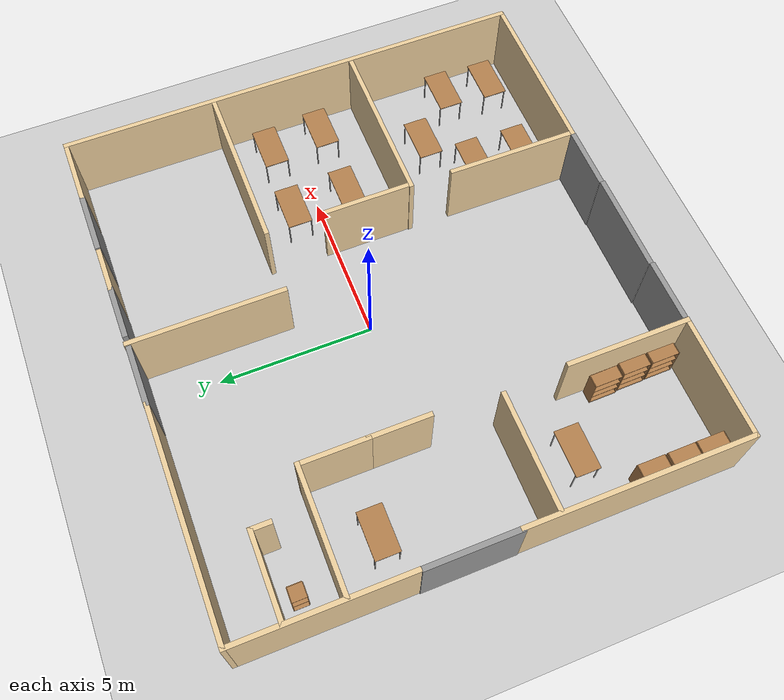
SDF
<sdf version="1.6">
 <world name="default">
  <light name="sun" type="directional">
   <pose>0 0 10 0 -0 0</pose>
   <diffuse>0.8 0.8 0.8 1</diffuse>
   <specular>0.2 0.2 0.2 1</specular>
   <attenuation>
    <range>1000</range>
    <constant>0.9</constant>
    <linear>0.01</linear>
    <quadratic>0.001</quadratic>
   </attenuation>
   <direction>-0.5 0.1 -0.9</direction>
  </light>
  <model name="ground_plane">
   <static>1</static>
   <link name="link">
    <collision name="collision">
     <geometry><plane><normal>0 0 1</normal><size>100 100</size></plane></geometry>
     <surface><friction><ode><mu>100</mu><mu2>50</mu2></ode></friction></surface>
    </collision>
    <visual name="visual">
     <cast_shadows>0</cast_shadows>
     <geometry><plane><normal>0 0 1</normal><size>100 100</size></plane></geometry>
     <material>
      <script><uri>file://media/materials/scripts/gazebo.material</uri><name>Gazebo/Grey</name></script>
     </material>
    </visual>
   </link>
  </model>
  <gravity>0 0 -9.8</gravity>
  <magnetic_field>6e-06 2.3e-05 -4.2e-05</magnetic_field>
  <atmosphere type="adiabatic"/>
  <physics name="default_physics" default="0" type="ode">
   <max_step_size>0.001</max_step_size>
   <real_time_factor>1</real_time_factor>
   <real_time_update_rate>1000</real_time_update_rate>
  </physics>
  <scene><ambient>0.4 0.4 0.4 1</ambient><background>0.7 0.7 0.7 1</background><shadows>1</shadows></scene>
  <audio><device>default</device></audio>
  <spherical_coordinates>
   <surface_model>EARTH_WGS84</surface_model>
   <latitude_deg>0</latitude_deg>
   <longitude_deg>0</longitude_deg>
   <elevation>0</elevation>
   <heading_deg>0</heading_deg>
  </spherical_coordinates>
  <model name="Building">
   <pose>0.22723 -0.57657 0 0 -0 0</pose>
   <link name="Door_1">
    <collision name="Door_1_Collision">
     <geometry><box><size>2 0.17 2.5</size></box></geometry>
     <pose>0 0 1.25 0 -0 0</pose>
    </collision>
    <visual name="Door_1_Visual">
     <pose>0 0 1.25 0 -0 0</pose>
     <geometry><box><size>2 0.17 2.5</size></box></geometry>
     <material>
      <script><uri>file://media/materials/scripts/gazebo.material</uri><name>Gazebo/Grey</name></script>
     </material>
    </visual>
    <pose>1.77302 -7.63321 0 0 -0 3.1393</pose>
   </link>
   <link name="Door_2">
    <collision name="Door_2_Collision">
     <geometry><box><size>2 0.17 2.5</size></box></geometry>
     <pose>0 0 1.25 0 -0 0</pose>
    </collision>
    <visual name="Door_2_Visual">
     <pose>0 0 1.25 0 -0 0</pose>
     <geometry><box><size>2 0.17 2.5</size></box></geometry>
     <material>
      <script><uri>file://media/materials/scripts/gazebo.material</uri><name>Gazebo/Grey</name></script>
     </material>
    </visual>
    <pose>-3.41797 -7.702 0 0 -0 -3.13381</pose>
   </link>
   <link name="Door_3">
    <collision name="Door_3_Collision">
     <geometry><box><size>1.75 0.17 2.5</size></box></geometry>
     <pose>0 0 1.25 0 -0 0</pose>
    </collision>
    <visual name="Door_3_Visual">
     <pose>0 0 1.25 0 -0 0</pose>
     <geometry><box><size>1.75 0.17 2.5</size></box></geometry>
     <material>
      <script><uri>file://media/materials/scripts/gazebo.material</uri><name>Gazebo/Grey</name></script>
     </material>
    </visual>
    <pose>1.87994 7.70603 0 0 -0 0</pose>
   </link>
   <link name="Wall_12">
    <collision name="Wall_12_Collision">
     <geometry><box><size>7.25 0.15 2.5</size></box></geometry>
     <pose>0 0 1.25 0 -0 0</pose>
    </collision>
    <visual name="Wall_12_Visual">
     <pose>0 0 1.25 0 -0 0</pose>
     <geometry><box><size>7.25 0.15 2.5</size></box></geometry>
     <material>
      <script><uri>file://media/materials/scripts/gazebo.material</uri><name>Gazebo/Grey</name></script>
      <ambient>0.921569 0.807843 0.615686 1</ambient>
     </material>
     <meta><layer>0</layer></meta>
    </visual>
    <pose>-8.3547 -4.19265 0 0 -0 -1.5708</pose>
   </link>
   <link name="Wall_14">
    <collision name="Wall_14_Collision">
     <geometry><box><size>7.25 0.15 2.5</size></box></geometry>
     <pose>0 0 1.25 0 -0 0</pose>
    </collision>
    <visual name="Wall_14_Visual">
     <pose>0 0 1.25 0 -0 0</pose>
     <geometry><box><size>7.25 0.15 2.5</size></box></geometry>
     <material>
      <script><uri>file://media/materials/scripts/gazebo.material</uri><name>Gazebo/Grey</name></script>
      <ambient>0.921569 0.807843 0.615686 1</ambient>
     </material>
     <meta><layer>0</layer></meta>
    </visual>
    <pose>-4.80157 7.70348 0 0 -0 0</pose>
   </link>
   <link name="Wall_16">
    <collision name="Wall_16_Collision">
     <geometry><box><size>5 0.15 2.5</size></box></geometry>
     <pose>0 0 1.25 0 -0 0</pose>
    </collision>
    <visual name="Wall_16_Visual">
     <pose>0 0 1.25 0 -0 0</pose>
     <geometry><box><size>5 0.15 2.5</size></box></geometry>
     <material>
      <script><uri>file://media/materials/scripts/gazebo.material</uri><name>Gazebo/Grey</name></script>
      <ambient>0.921569 0.807843 0.615686 1</ambient>
     </material>
     <meta><layer>0</layer></meta>
    </visual>
    <pose>0.791999 5.31765 0 0 -0 -1.5708</pose>
   </link>
   <link name="Wall_18">
    <collision name="Wall_18_Collision">
     <geometry><box><size>2.75 0.15 2.5</size></box></geometry>
     <pose>0 0 1.25 0 -0 0</pose>
    </collision>
    <visual name="Wall_18_Visual">
     <pose>0 0 1.25 0 -0 0</pose>
     <geometry><box><size>2.75 0.15 2.5</size></box></geometry>
     <material>
      <script><uri>file://media/materials/scripts/gazebo.material</uri><name>Gazebo/Grey</name></script>
      <ambient>0.921569 0.807843 0.615686 1</ambient>
     </material>
     <meta><layer>0</layer></meta>
    </visual>
    <pose>-7.02626 6.10787 0 0 -0 0</pose>
   </link>
   <link name="Wall_19">
    <collision name="Wall_19_Collision">
     <geometry><box><size>0.7 0.15 2.5</size></box></geometry>
     <pose>0 0 1.25 0 -0 0</pose>
    </collision>
    <visual name="Wall_19_Visual">
     <pose>0 0 1.25 0 -0 0</pose>
     <geometry><box><size>0.7 0.15 2.5</size></box></geometry>
     <material>
      <script><uri>file://media/materials/scripts/gazebo.material</uri><name>Gazebo/Grey</name></script>
      <ambient>0.921569 0.807843 0.615686 1</ambient>
     </material>
     <meta><layer>0</layer></meta>
    </visual>
    <pose>-5.72626 5.83287 0 0 -0 -1.5708</pose>
   </link>
   <link name="Wall_23">
    <collision name="Wall_23_Collision">
     <geometry><box><size>4 0.15 2.5</size></box></geometry>
     <pose>0 0 1.25 0 -0 0</pose>
    </collision>
    <visual name="Wall_23_Visual">
     <pose>0 0 1.25 0 -0 0</pose>
     <geometry><box><size>4 0.15 2.5</size></box></geometry>
     <material>
      <script><uri>file://media/materials/scripts/gazebo.material</uri><name>Gazebo/Grey</name></script>
      <ambient>0.921569 0.807843 0.615686 1</ambient>
     </material>
     <meta><layer>0</layer></meta>
    </visual>
    <pose>-6.40126 4.34787 0 0 -0 0</pose>
   </link>
   <link name="Wall_24">
    <collision name="Wall_24_Collision">
     <geometry><box><size>2.25 0.15 2.5</size></box></geometry>
     <pose>0 0 1.25 0 -0 0</pose>
    </collision>
    <visual name="Wall_24_Visual">
     <pose>0 0 1.25 0 -0 0</pose>
     <geometry><box><size>2.25 0.15 2.5</size></box></geometry>
     <material>
      <script><uri>file://media/materials/scripts/gazebo.material</uri><name>Gazebo/Grey</name></script>
      <ambient>0.921569 0.807843 0.615686 1</ambient>
     </material>
     <meta><layer>0</layer></meta>
    </visual>
    <pose>-4.47626 3.29787 0 0 -0 -1.5708</pose>
   </link>
   <link name="Wall_26">
    <collision name="Wall_26_Collision">
     <geometry><box><size>1.5 0.15 2.5</size></box></geometry>
     <pose>0 0 1.25 0 -0 0</pose>
    </collision>
    <visual name="Wall_26_Visual">
     <pose>0 0 1.25 0 -0 0</pose>
     <geometry><box><size>1.5 0.15 2.5</size></box></geometry>
     <material>
      <script><uri>file://media/materials/scripts/gazebo.material</uri><name>Gazebo/Grey</name></script>
      <ambient>0.921569 0.807843 0.615686 1</ambient>
     </material>
     <meta><layer>0</layer></meta>
    </visual>
    <pose>3.42874 7.70787 0 0 -0 0</pose>
   </link>
   <link name="Wall_28">
    <collision name="Wall_28_Collision">
     <geometry><box><size>2.25 0.15 2.5</size></box></geometry>
     <pose>0 0 1.25 0 -0 0</pose>
    </collision>
    <visual name="Wall_28_Visual">
     <pose>0 0 1.25 0 -0 0</pose>
     <geometry><box><size>2.25 0.15 2.5</size></box></geometry>
     <material>
      <script><uri>file://media/materials/scripts/gazebo.material</uri><name>Gazebo/Grey</name></script>
      <ambient>0.921569 0.807843 0.615686 1</ambient>
     </material>
     <meta><layer>0</layer></meta>
    </visual>
    <pose>7.30468 7.71385 0 0 -0 0</pose>
   </link>
   <link name="Wall_29">
    <collision name="Wall_29_Collision">
     <geometry><box><size>15.5 0.15 2.5</size></box></geometry>
     <pose>0 0 1.25 0 -0 0</pose>
    </collision>
    <visual name="Wall_29_Visual">
     <pose>0 0 1.25 0 -0 0</pose>
     <geometry><box><size>15.5 0.15 2.5</size></box></geometry>
     <material>
      <script><uri>file://media/materials/scripts/gazebo.material</uri><name>Gazebo/Grey</name></script>
      <ambient>0.921569 0.807843 0.615686 1</ambient>
     </material>
     <meta><layer>0</layer></meta>
    </visual>
    <pose>8.35468 0.038854 0 0 -0 -1.5708</pose>
   </link>
   <link name="Wall_31">
    <collision name="Wall_31_Collision">
     <geometry><box><size>3.75 0.15 2.5</size></box></geometry>
     <pose>0 0 1.25 0 -0 0</pose>
    </collision>
    <visual name="Wall_31_Visual">
     <pose>0 0 1.25 0 -0 0</pose>
     <geometry><box><size>3.75 0.15 2.5</size></box></geometry>
     <material>
      <script><uri>file://media/materials/scripts/gazebo.material</uri><name>Gazebo/Grey</name></script>
      <ambient>0.921569 0.807843 0.615686 1</ambient>
     </material>
     <meta><layer>0</layer></meta>
    </visual>
    <pose>-6.46277 -1.77396 0 0 -0 0</pose>
   </link>
   <link name="Wall_33">
    <collision name="Wall_33_Collision">
     <geometry><box><size>2 0.15 2.5</size></box></geometry>
     <pose>0 0 1.25 0 -0 0</pose>
    </collision>
    <visual name="Wall_33_Visual">
     <pose>0 0 1.25 0 -0 0</pose>
     <geometry><box><size>2 0.15 2.5</size></box></geometry>
     <material>
      <script><uri>file://media/materials/scripts/gazebo.material</uri><name>Gazebo/Grey</name></script>
      <ambient>0.921569 0.807843 0.615686 1</ambient>
     </material>
     <meta><layer>0</layer></meta>
    </visual>
    <pose>-4.47626 1.32287 0 0 -0 -1.5708</pose>
   </link>
   <link name="Wall_35">
    <collision name="Wall_35_Collision">
     <geometry><box><size>5.5 0.15 2.5</size></box></geometry>
     <pose>0 0 1.25 0 -0 0</pose>
    </collision>
    <visual name="Wall_35_Visual">
     <pose>0 0 1.25 0 -0 0</pose>
     <geometry><box><size>5.5 0.15 2.5</size></box></geometry>
     <material>
      <script><uri>file://media/materials/scripts/gazebo.material</uri><name>Gazebo/Grey</name></script>
      <ambient>0.921569 0.807843 0.615686 1</ambient>
     </material>
     <meta><layer>0</layer></meta>
    </visual>
    <pose>5.58136 2.77318 0 0 -0 0</pose>
   </link>
   <link name="Wall_38">
    <collision name="Wall_38_Collision">
     <geometry><box><size>3 0.15 2.5</size></box></geometry>
     <pose>0 0 1.25 0 -0 0</pose>
    </collision>
    <visual name="Wall_38_Visual">
     <pose>0 0 1.25 0 -0 0</pose>
     <geometry><box><size>3 0.15 2.5</size></box></geometry>
     <material>
      <script><uri>file://media/materials/scripts/gazebo.material</uri><name>Gazebo/Grey</name></script>
      <ambient>0.921569 0.807843 0.615686 1</ambient>
     </material>
     <meta><layer>0</layer></meta>
    </visual>
    <pose>2.90822 -0.593394 0 0 -0 -1.5708</pose>
   </link>
   <link name="Wall_39">
    <collision name="Wall_39_Collision">
     <geometry><box><size>5.46978 0.15 2.5</size></box></geometry>
     <pose>0 0 1.25 0 -0 0</pose>
    </collision>
    <visual name="Wall_39_Visual">
     <pose>0 0 1.25 0 -0 0</pose>
     <geometry><box><size>5.46978 0.15 2.5</size></box></geometry>
     <material>
      <script><uri>file://media/materials/scripts/gazebo.material</uri><name>Gazebo/Grey</name></script>
      <ambient>0.921569 0.807843 0.615686 1</ambient>
     </material>
     <meta><layer>0</layer></meta>
    </visual>
    <pose>5.53786 -2.02643 0 0 -0 -0.00302</pose>
   </link>
   <link name="Wall_42">
    <collision name="Wall_42_Collision">
     <geometry><box><size>5.65695 0.15 2.5</size></box></geometry>
     <pose>0 0 1.25 0 -0 0</pose>
    </collision>
    <visual name="Wall_42_Visual">
     <pose>0 0 1.25 0 -0 0</pose>
     <geometry><box><size>5.65695 0.15 2.5</size></box></geometry>
     <material>
      <script><uri>file://media/materials/scripts/gazebo.material</uri><name>Gazebo/Grey</name></script>
      <ambient>0.921569 0.807843 0.615686 1</ambient>
     </material>
     <meta><layer>0</layer></meta>
    </visual>
    <pose>5.60121 -7.6353 0 0 -0 -0.000306</pose>
   </link>
   <link name="Wall_44">
    <collision name="Wall_44_Collision">
     <geometry><box><size>4.34305 0.15 2.5</size></box></geometry>
     <pose>0 0 1.25 0 -0 0</pose>
    </collision>
    <visual name="Wall_44_Visual">
     <pose>0 0 1.25 0 -0 0</pose>
     <geometry><box><size>4.34305 0.15 2.5</size></box></geometry>
     <material>
      <script><uri>file://media/materials/scripts/gazebo.material</uri><name>Gazebo/Grey</name></script>
      <ambient>0.921569 0.807843 0.615686 1</ambient>
     </material>
     <meta><layer>0</layer></meta>
    </visual>
    <pose>2.85823 -5.53796 0 0 -0 -1.5758</pose>
   </link>
   <link name="Wall_46">
    <collision name="Wall_46_Collision">
     <geometry><box><size>4 0.15 2.5</size></box></geometry>
     <pose>0 0 1.25 0 -0 0</pose>
    </collision>
    <visual name="Wall_46_Visual">
     <pose>0 0 1.25 0 -0 0</pose>
     <geometry><box><size>4 0.15 2.5</size></box></geometry>
     <material>
      <script><uri>file://media/materials/scripts/gazebo.material</uri><name>Gazebo/Grey</name></script>
      <ambient>0.921569 0.807843 0.615686 1</ambient>
     </material>
     <meta><layer>0</layer></meta>
    </visual>
    <pose>-6.42971 -7.74265 0 0 -0 0</pose>
   </link>
   <link name="Wall_48">
    <collision name="Wall_48_Collision">
     <geometry><box><size>4 0.15 2.5</size></box></geometry>
     <pose>0 0 1.25 0 -0 0</pose>
    </collision>
    <visual name="Wall_48_Visual">
     <pose>0 0 1.25 0 -0 0</pose>
     <geometry><box><size>4 0.15 2.5</size></box></geometry>
     <material>
      <script><uri>file://media/materials/scripts/gazebo.material</uri><name>Gazebo/Grey</name></script>
      <ambient>0.921569 0.807843 0.615686 1</ambient>
     </material>
     <meta><layer>0</layer></meta>
    </visual>
    <pose>-4.50471 -5.81765 0 0 -0 1.5708</pose>
   </link>
   <link name="Wall_9">
    <collision name="Wall_9_Collision">
     <geometry><box><size>5.5 0.15 2.5</size></box></geometry>
     <pose>0 0 1.25 0 -0 0</pose>
    </collision>
    <visual name="Wall_9_Visual">
     <pose>0 0 1.25 0 -0 0</pose>
     <geometry><box><size>5.5 0.15 2.5</size></box></geometry>
     <material>
      <script><uri>file://media/materials/scripts/gazebo.material</uri><name>Gazebo/Grey</name></script>
      <ambient>0.921569 0.807843 0.615686 1</ambient>
     </material>
     <meta><layer>0</layer></meta>
    </visual>
    <pose>-8.35157 5.02848 0 0 -0 -1.5708</pose>
   </link>
   <link name="Window_2">
    <collision name="Window_2_Collision">
     <geometry><box><size>3 0.17 2.5</size></box></geometry>
     <pose>0 0 1.25 0 -0 0</pose>
    </collision>
    <visual name="Window_2_Visual">
     <pose>0 0 1.25 0 -0 0</pose>
     <geometry><box><size>3 0.17 2.5</size></box></geometry>
     <material>
      <script><uri>file://media/materials/scripts/gazebo.material</uri><name>Gazebo/Grey</name></script>
     </material>
    </visual>
    <pose>-8.3671 0.789602 0 0 0 -1.5705</pose>
   </link>
   <link name="Window_3">
    <collision name="Window_3_Collision">
     <geometry><box><size>2 0.17 2.5</size></box></geometry>
     <pose>0 0 1.25 0 -0 0</pose>
    </collision>
    <visual name="Window_3_Visual">
     <pose>0 0 1.25 0 -0 0</pose>
     <geometry><box><size>2 0.17 2.5</size></box></geometry>
     <material>
      <script><uri>file://media/materials/scripts/gazebo.material</uri><name>Gazebo/Grey</name></script>
     </material>
    </visual>
    <pose>5.22216 7.70864 0 0 -0 0</pose>
   </link>
   <link name="Window_4">
    <collision name="Window_4_Collision">
     <geometry><box><size>3.2 0.17 2.5</size></box></geometry>
     <pose>0 0 1.25 0 -0 0</pose>
    </collision>
    <visual name="Window_4_Visual">
     <pose>0 0 1.25 0 -0 0</pose>
     <geometry><box><size>3.2 0.17 2.5</size></box></geometry>
     <material>
      <script><uri>file://media/materials/scripts/gazebo.material</uri><name>Gazebo/Grey</name></script>
     </material>
    </visual>
    <pose>-0.82762 -7.66069 0 0 -0 0</pose>
   </link>
   <link name="Window_5">
    <collision name="Window_5_Collision">
     <geometry><box><size>2 0.17 2.5</size></box></geometry>
     <pose>0 0 1.25 0 -0 0</pose>
    </collision>
    <visual name="Window_5_Visual">
     <pose>0 0 1.25 0 -0 0</pose>
     <geometry><box><size>2 0.17 2.5</size></box></geometry>
     <material>
      <script><uri>file://media/materials/scripts/gazebo.material</uri><name>Gazebo/Grey</name></script>
     </material>
    </visual>
    <pose>-0.31136 7.70603 0 0 -0 0</pose>
   </link>
   <static>1</static>
  </model>
  <model name="bookshelf">
   <static>1</static>
   <link name="link">
    <inertial><mass>1</mass></inertial>
    <collision name="back">
     <pose>0 0.005 0.6 0 -0 0</pose>
     <geometry><box><size>0.9 0.01 1.2</size></box></geometry>
    </collision>
    <visual name="visual1">
     <pose>0 0.005 0.6 0 -0 0</pose>
     <geometry><box><size>0.9 0.01 1.2</size></box></geometry>
     <material>
      <script><uri>file://media/materials/scripts/gazebo.material</uri><name>Gazebo/Wood</name></script>
     </material>
    </visual>
    <collision name="left_side">
     <pose>0.45 -0.195 0.6 0 -0 0</pose>
     <geometry><box><size>0.02 0.4 1.2</size></box></geometry>
    </collision>
    <visual name="visual2">
     <pose>0.45 -0.195 0.6 0 -0 0</pose>
     <geometry><box><size>0.02 0.4 1.2</size></box></geometry>
     <material>
      <script><uri>file://media/materials/scripts/gazebo.material</uri><name>Gazebo/Wood</name></script>
     </material>
    </visual>
    <collision name="right_side">
     <pose>-0.45 -0.195 0.6 0 -0 0</pose>
     <geometry><box><size>0.02 0.4 1.2</size></box></geometry>
    </collision>
    <visual name="visual3">
     <pose>-0.45 -0.195 0.6 0 -0 0</pose>
     <geometry><box><size>0.02 0.4 1.2</size></box></geometry>
     <material>
      <script><uri>file://media/materials/scripts/gazebo.material</uri><name>Gazebo/Wood</name></script>
     </material>
    </visual>
    <collision name="bottom">
     <pose>0 -0.195 0.03 0 -0 0</pose>
     <geometry><box><size>0.88 0.4 0.06</size></box></geometry>
    </collision>
    <visual name="visual4">
     <pose>0 -0.195 0.03 0 -0 0</pose>
     <geometry><box><size>0.88 0.4 0.06</size></box></geometry>
     <material>
      <script><uri>file://media/materials/scripts/gazebo.material</uri><name>Gazebo/Wood</name></script>
     </material>
    </visual>
    <collision name="top">
     <pose>0 -0.195 1.19 0 -0 0</pose>
     <geometry><box><size>0.88 0.4 0.02</size></box></geometry>
    </collision>
    <visual name="visual5">
     <pose>0 -0.195 1.19 0 -0 0</pose>
     <geometry><box><size>0.88 0.4 0.02</size></box></geometry>
     <material>
      <script><uri>file://media/materials/scripts/gazebo.material</uri><name>Gazebo/Wood</name></script>
     </material>
    </visual>
    <collision name="low_shelf">
     <pose>0 -0.195 0.43 0 -0 0</pose>
     <geometry><box><size>0.88 0.4 0.02</size></box></geometry>
    </collision>
    <visual name="visual6">
     <pose>0 -0.195 0.43 0 -0 0</pose>
     <geometry><box><size>0.88 0.4 0.02</size></box></geometry>
     <material>
      <script><uri>file://media/materials/scripts/gazebo.material</uri><name>Gazebo/Wood</name></script>
     </material>
    </visual>
    <collision name="high_shelf">
     <pose>0 -0.195 0.8 0 -0 0</pose>
     <geometry><box><size>0.88 0.4 0.02</size></box></geometry>
    </collision>
    <visual name="visual7">
     <pose>0 -0.195 0.8 0 -0 0</pose>
     <geometry><box><size>0.88 0.4 0.02</size></box></geometry>
     <material>
      <script><uri>file://media/materials/scripts/gazebo.material</uri><name>Gazebo/Wood</name></script>
     </material>
    </visual>
   </link>
   <pose>-7.78136 -7.6809 0 0 -0 1.57147</pose>
  </model>
  <model name="bookshelf_clone">
   <static>1</static>
   <link name="link">
    <inertial><mass>1</mass></inertial>
    <collision name="back">
     <pose>0 0.005 0.6 0 -0 0</pose>
     <geometry><box><size>0.9 0.01 1.2</size></box></geometry>
    </collision>
    <visual name="visual1">
     <pose>0 0.005 0.6 0 -0 0</pose>
     <geometry><box><size>0.9 0.01 1.2</size></box></geometry>
     <material>
      <script><uri>file://media/materials/scripts/gazebo.material</uri><name>Gazebo/Wood</name></script>
     </material>
    </visual>
    <collision name="left_side">
     <pose>0.45 -0.195 0.6 0 -0 0</pose>
     <geometry><box><size>0.02 0.4 1.2</size></box></geometry>
    </collision>
    <visual name="visual2">
     <pose>0.45 -0.195 0.6 0 -0 0</pose>
     <geometry><box><size>0.02 0.4 1.2</size></box></geometry>
     <material>
      <script><uri>file://media/materials/scripts/gazebo.material</uri><name>Gazebo/Wood</name></script>
     </material>
    </visual>
    <collision name="right_side">
     <pose>-0.45 -0.195 0.6 0 -0 0</pose>
     <geometry><box><size>0.02 0.4 1.2</size></box></geometry>
    </collision>
    <visual name="visual3">
     <pose>-0.45 -0.195 0.6 0 -0 0</pose>
     <geometry><box><size>0.02 0.4 1.2</size></box></geometry>
     <material>
      <script><uri>file://media/materials/scripts/gazebo.material</uri><name>Gazebo/Wood</name></script>
     </material>
    </visual>
    <collision name="bottom">
     <pose>0 -0.195 0.03 0 -0 0</pose>
     <geometry><box><size>0.88 0.4 0.06</size></box></geometry>
    </collision>
    <visual name="visual4">
     <pose>0 -0.195 0.03 0 -0 0</pose>
     <geometry><box><size>0.88 0.4 0.06</size></box></geometry>
     <material>
      <script><uri>file://media/materials/scripts/gazebo.material</uri><name>Gazebo/Wood</name></script>
     </material>
    </visual>
    <collision name="top">
     <pose>0 -0.195 1.19 0 -0 0</pose>
     <geometry><box><size>0.88 0.4 0.02</size></box></geometry>
    </collision>
    <visual name="visual5">
     <pose>0 -0.195 1.19 0 -0 0</pose>
     <geometry><box><size>0.88 0.4 0.02</size></box></geometry>
     <material>
      <script><uri>file://media/materials/scripts/gazebo.material</uri><name>Gazebo/Wood</name></script>
     </material>
    </visual>
    <collision name="low_shelf">
     <pose>0 -0.195 0.43 0 -0 0</pose>
     <geometry><box><size>0.88 0.4 0.02</size></box></geometry>
    </collision>
    <visual name="visual6">
     <pose>0 -0.195 0.43 0 -0 0</pose>
     <geometry><box><size>0.88 0.4 0.02</size></box></geometry>
     <material>
      <script><uri>file://media/materials/scripts/gazebo.material</uri><name>Gazebo/Wood</name></script>
     </material>
    </visual>
    <collision name="high_shelf">
     <pose>0 -0.195 0.8 0 -0 0</pose>
     <geometry><box><size>0.88 0.4 0.02</size></box></geometry>
    </collision>
    <visual name="visual7">
     <pose>0 -0.195 0.8 0 -0 0</pose>
     <geometry><box><size>0.88 0.4 0.02</size></box></geometry>
     <material>
      <script><uri>file://media/materials/scripts/gazebo.material</uri><name>Gazebo/Wood</name></script>
     </material>
    </visual>
   </link>
   <pose>-7.78423 -6.74163 0 0 -0 1.57147</pose>
  </model>
  <model name="bookshelf_clone_0">
   <static>1</static>
   <link name="link">
    <inertial><mass>1</mass></inertial>
    <collision name="back">
     <pose>0 0.005 0.6 0 -0 0</pose>
     <geometry><box><size>0.9 0.01 1.2</size></box></geometry>
    </collision>
    <visual name="visual1">
     <pose>0 0.005 0.6 0 -0 0</pose>
     <geometry><box><size>0.9 0.01 1.2</size></box></geometry>
     <material>
      <script><uri>file://media/materials/scripts/gazebo.material</uri><name>Gazebo/Wood</name></script>
     </material>
    </visual>
    <collision name="left_side">
     <pose>0.45 -0.195 0.6 0 -0 0</pose>
     <geometry><box><size>0.02 0.4 1.2</size></box></geometry>
    </collision>
    <visual name="visual2">
     <pose>0.45 -0.195 0.6 0 -0 0</pose>
     <geometry><box><size>0.02 0.4 1.2</size></box></geometry>
     <material>
      <script><uri>file://media/materials/scripts/gazebo.material</uri><name>Gazebo/Wood</name></script>
     </material>
    </visual>
    <collision name="right_side">
     <pose>-0.45 -0.195 0.6 0 -0 0</pose>
     <geometry><box><size>0.02 0.4 1.2</size></box></geometry>
    </collision>
    <visual name="visual3">
     <pose>-0.45 -0.195 0.6 0 -0 0</pose>
     <geometry><box><size>0.02 0.4 1.2</size></box></geometry>
     <material>
      <script><uri>file://media/materials/scripts/gazebo.material</uri><name>Gazebo/Wood</name></script>
     </material>
    </visual>
    <collision name="bottom">
     <pose>0 -0.195 0.03 0 -0 0</pose>
     <geometry><box><size>0.88 0.4 0.06</size></box></geometry>
    </collision>
    <visual name="visual4">
     <pose>0 -0.195 0.03 0 -0 0</pose>
     <geometry><box><size>0.88 0.4 0.06</size></box></geometry>
     <material>
      <script><uri>file://media/materials/scripts/gazebo.material</uri><name>Gazebo/Wood</name></script>
     </material>
    </visual>
    <collision name="top">
     <pose>0 -0.195 1.19 0 -0 0</pose>
     <geometry><box><size>0.88 0.4 0.02</size></box></geometry>
    </collision>
    <visual name="visual5">
     <pose>0 -0.195 1.19 0 -0 0</pose>
     <geometry><box><size>0.88 0.4 0.02</size></box></geometry>
     <material>
      <script><uri>file://media/materials/scripts/gazebo.material</uri><name>Gazebo/Wood</name></script>
     </material>
    </visual>
    <collision name="low_shelf">
     <pose>0 -0.195 0.43 0 -0 0</pose>
     <geometry><box><size>0.88 0.4 0.02</size></box></geometry>
    </collision>
    <visual name="visual6">
     <pose>0 -0.195 0.43 0 -0 0</pose>
     <geometry><box><size>0.88 0.4 0.02</size></box></geometry>
     <material>
      <script><uri>file://media/materials/scripts/gazebo.material</uri><name>Gazebo/Wood</name></script>
     </material>
    </visual>
    <collision name="high_shelf">
     <pose>0 -0.195 0.8 0 -0 0</pose>
     <geometry><box><size>0.88 0.4 0.02</size></box></geometry>
    </collision>
    <visual name="visual7">
     <pose>0 -0.195 0.8 0 -0 0</pose>
     <geometry><box><size>0.88 0.4 0.02</size></box></geometry>
     <material>
      <script><uri>file://media/materials/scripts/gazebo.material</uri><name>Gazebo/Wood</name></script>
     </material>
    </visual>
   </link>
   <pose>-7.78677 -5.75368 0 0 -0 1.57147</pose>
  </model>
  <model name="bookshelf_clone_1">
   <static>1</static>
   <link name="link">
    <inertial><mass>1</mass></inertial>
    <collision name="back">
     <pose>0 0.005 0.6 0 -0 0</pose>
     <geometry><box><size>0.9 0.01 1.2</size></box></geometry>
    </collision>
    <visual name="visual1">
     <pose>0 0.005 0.6 0 -0 0</pose>
     <geometry><box><size>0.9 0.01 1.2</size></box></geometry>
     <material>
      <script><uri>file://media/materials/scripts/gazebo.material</uri><name>Gazebo/Wood</name></script>
     </material>
    </visual>
    <collision name="left_side">
     <pose>0.45 -0.195 0.6 0 -0 0</pose>
     <geometry><box><size>0.02 0.4 1.2</size></box></geometry>
    </collision>
    <visual name="visual2">
     <pose>0.45 -0.195 0.6 0 -0 0</pose>
     <geometry><box><size>0.02 0.4 1.2</size></box></geometry>
     <material>
      <script><uri>file://media/materials/scripts/gazebo.material</uri><name>Gazebo/Wood</name></script>
     </material>
    </visual>
    <collision name="right_side">
     <pose>-0.45 -0.195 0.6 0 -0 0</pose>
     <geometry><box><size>0.02 0.4 1.2</size></box></geometry>
    </collision>
    <visual name="visual3">
     <pose>-0.45 -0.195 0.6 0 -0 0</pose>
     <geometry><box><size>0.02 0.4 1.2</size></box></geometry>
     <material>
      <script><uri>file://media/materials/scripts/gazebo.material</uri><name>Gazebo/Wood</name></script>
     </material>
    </visual>
    <collision name="bottom">
     <pose>0 -0.195 0.03 0 -0 0</pose>
     <geometry><box><size>0.88 0.4 0.06</size></box></geometry>
    </collision>
    <visual name="visual4">
     <pose>0 -0.195 0.03 0 -0 0</pose>
     <geometry><box><size>0.88 0.4 0.06</size></box></geometry>
     <material>
      <script><uri>file://media/materials/scripts/gazebo.material</uri><name>Gazebo/Wood</name></script>
     </material>
    </visual>
    <collision name="top">
     <pose>0 -0.195 1.19 0 -0 0</pose>
     <geometry><box><size>0.88 0.4 0.02</size></box></geometry>
    </collision>
    <visual name="visual5">
     <pose>0 -0.195 1.19 0 -0 0</pose>
     <geometry><box><size>0.88 0.4 0.02</size></box></geometry>
     <material>
      <script><uri>file://media/materials/scripts/gazebo.material</uri><name>Gazebo/Wood</name></script>
     </material>
    </visual>
    <collision name="low_shelf">
     <pose>0 -0.195 0.43 0 -0 0</pose>
     <geometry><box><size>0.88 0.4 0.02</size></box></geometry>
    </collision>
    <visual name="visual6">
     <pose>0 -0.195 0.43 0 -0 0</pose>
     <geometry><box><size>0.88 0.4 0.02</size></box></geometry>
     <material>
      <script><uri>file://media/materials/scripts/gazebo.material</uri><name>Gazebo/Wood</name></script>
     </material>
    </visual>
    <collision name="high_shelf">
     <pose>0 -0.195 0.8 0 -0 0</pose>
     <geometry><box><size>0.88 0.4 0.02</size></box></geometry>
    </collision>
    <visual name="visual7">
     <pose>0 -0.195 0.8 0 -0 0</pose>
     <geometry><box><size>0.88 0.4 0.02</size></box></geometry>
     <material>
      <script><uri>file://media/materials/scripts/gazebo.material</uri><name>Gazebo/Wood</name></script>
     </material>
    </visual>
   </link>
   <pose>-4.33405 -7.70418 0 0 0 -1.5643</pose>
  </model>
  <model name="bookshelf_clone_1_clone">
   <static>1</static>
   <link name="link">
    <inertial><mass>1</mass></inertial>
    <collision name="back">
     <pose>0 0.005 0.6 0 -0 0</pose>
     <geometry><box><size>0.9 0.01 1.2</size></box></geometry>
    </collision>
    <visual name="visual1">
     <pose>0 0.005 0.6 0 -0 0</pose>
     <geometry><box><size>0.9 0.01 1.2</size></box></geometry>
     <material>
      <script><uri>file://media/materials/scripts/gazebo.material</uri><name>Gazebo/Wood</name></script>
     </material>
    </visual>
    <collision name="left_side">
     <pose>0.45 -0.195 0.6 0 -0 0</pose>
     <geometry><box><size>0.02 0.4 1.2</size></box></geometry>
    </collision>
    <visual name="visual2">
     <pose>0.45 -0.195 0.6 0 -0 0</pose>
     <geometry><box><size>0.02 0.4 1.2</size></box></geometry>
     <material>
      <script><uri>file://media/materials/scripts/gazebo.material</uri><name>Gazebo/Wood</name></script>
     </material>
    </visual>
    <collision name="right_side">
     <pose>-0.45 -0.195 0.6 0 -0 0</pose>
     <geometry><box><size>0.02 0.4 1.2</size></box></geometry>
    </collision>
    <visual name="visual3">
     <pose>-0.45 -0.195 0.6 0 -0 0</pose>
     <geometry><box><size>0.02 0.4 1.2</size></box></geometry>
     <material>
      <script><uri>file://media/materials/scripts/gazebo.material</uri><name>Gazebo/Wood</name></script>
     </material>
    </visual>
    <collision name="bottom">
     <pose>0 -0.195 0.03 0 -0 0</pose>
     <geometry><box><size>0.88 0.4 0.06</size></box></geometry>
    </collision>
    <visual name="visual4">
     <pose>0 -0.195 0.03 0 -0 0</pose>
     <geometry><box><size>0.88 0.4 0.06</size></box></geometry>
     <material>
      <script><uri>file://media/materials/scripts/gazebo.material</uri><name>Gazebo/Wood</name></script>
     </material>
    </visual>
    <collision name="top">
     <pose>0 -0.195 1.19 0 -0 0</pose>
     <geometry><box><size>0.88 0.4 0.02</size></box></geometry>
    </collision>
    <visual name="visual5">
     <pose>0 -0.195 1.19 0 -0 0</pose>
     <geometry><box><size>0.88 0.4 0.02</size></box></geometry>
     <material>
      <script><uri>file://media/materials/scripts/gazebo.material</uri><name>Gazebo/Wood</name></script>
     </material>
    </visual>
    <collision name="low_shelf">
     <pose>0 -0.195 0.43 0 -0 0</pose>
     <geometry><box><size>0.88 0.4 0.02</size></box></geometry>
    </collision>
    <visual name="visual6">
     <pose>0 -0.195 0.43 0 -0 0</pose>
     <geometry><box><size>0.88 0.4 0.02</size></box></geometry>
     <material>
      <script><uri>file://media/materials/scripts/gazebo.material</uri><name>Gazebo/Wood</name></script>
     </material>
    </visual>
    <collision name="high_shelf">
     <pose>0 -0.195 0.8 0 -0 0</pose>
     <geometry><box><size>0.88 0.4 0.02</size></box></geometry>
    </collision>
    <visual name="visual7">
     <pose>0 -0.195 0.8 0 -0 0</pose>
     <geometry><box><size>0.88 0.4 0.02</size></box></geometry>
     <material>
      <script><uri>file://media/materials/scripts/gazebo.material</uri><name>Gazebo/Wood</name></script>
     </material>
    </visual>
   </link>
   <pose>-4.35252 -6.73795 0 0 0 -1.5643</pose>
  </model>
  <model name="bookshelf_clone_1_clone_0">
   <static>1</static>
   <link name="link">
    <inertial><mass>1</mass></inertial>
    <collision name="back">
     <pose>0 0.005 0.6 0 -0 0</pose>
     <geometry><box><size>0.9 0.01 1.2</size></box></geometry>
    </collision>
    <visual name="visual1">
     <pose>0 0.005 0.6 0 -0 0</pose>
     <geometry><box><size>0.9 0.01 1.2</size></box></geometry>
     <material>
      <script><uri>file://media/materials/scripts/gazebo.material</uri><name>Gazebo/Wood</name></script>
     </material>
    </visual>
    <collision name="left_side">
     <pose>0.45 -0.195 0.6 0 -0 0</pose>
     <geometry><box><size>0.02 0.4 1.2</size></box></geometry>
    </collision>
    <visual name="visual2">
     <pose>0.45 -0.195 0.6 0 -0 0</pose>
     <geometry><box><size>0.02 0.4 1.2</size></box></geometry>
     <material>
      <script><uri>file://media/materials/scripts/gazebo.material</uri><name>Gazebo/Wood</name></script>
     </material>
    </visual>
    <collision name="right_side">
     <pose>-0.45 -0.195 0.6 0 -0 0</pose>
     <geometry><box><size>0.02 0.4 1.2</size></box></geometry>
    </collision>
    <visual name="visual3">
     <pose>-0.45 -0.195 0.6 0 -0 0</pose>
     <geometry><box><size>0.02 0.4 1.2</size></box></geometry>
     <material>
      <script><uri>file://media/materials/scripts/gazebo.material</uri><name>Gazebo/Wood</name></script>
     </material>
    </visual>
    <collision name="bottom">
     <pose>0 -0.195 0.03 0 -0 0</pose>
     <geometry><box><size>0.88 0.4 0.06</size></box></geometry>
    </collision>
    <visual name="visual4">
     <pose>0 -0.195 0.03 0 -0 0</pose>
     <geometry><box><size>0.88 0.4 0.06</size></box></geometry>
     <material>
      <script><uri>file://media/materials/scripts/gazebo.material</uri><name>Gazebo/Wood</name></script>
     </material>
    </visual>
    <collision name="top">
     <pose>0 -0.195 1.19 0 -0 0</pose>
     <geometry><box><size>0.88 0.4 0.02</size></box></geometry>
    </collision>
    <visual name="visual5">
     <pose>0 -0.195 1.19 0 -0 0</pose>
     <geometry><box><size>0.88 0.4 0.02</size></box></geometry>
     <material>
      <script><uri>file://media/materials/scripts/gazebo.material</uri><name>Gazebo/Wood</name></script>
     </material>
    </visual>
    <collision name="low_shelf">
     <pose>0 -0.195 0.43 0 -0 0</pose>
     <geometry><box><size>0.88 0.4 0.02</size></box></geometry>
    </collision>
    <visual name="visual6">
     <pose>0 -0.195 0.43 0 -0 0</pose>
     <geometry><box><size>0.88 0.4 0.02</size></box></geometry>
     <material>
      <script><uri>file://media/materials/scripts/gazebo.material</uri><name>Gazebo/Wood</name></script>
     </material>
    </visual>
    <collision name="high_shelf">
     <pose>0 -0.195 0.8 0 -0 0</pose>
     <geometry><box><size>0.88 0.4 0.02</size></box></geometry>
    </collision>
    <visual name="visual7">
     <pose>0 -0.195 0.8 0 -0 0</pose>
     <geometry><box><size>0.88 0.4 0.02</size></box></geometry>
     <material>
      <script><uri>file://media/materials/scripts/gazebo.material</uri><name>Gazebo/Wood</name></script>
     </material>
    </visual>
   </link>
   <pose>-4.3991 -5.76129 0 0 0 -1.5643</pose>
  </model>
  <model name="table">
   <static>1</static>
   <link name="link">
    <collision name="surface">
     <pose>0 0 1 0 -0 0</pose>
     <geometry><box><size>1.5 0.8 0.03</size></box></geometry>
     <surface><friction><ode><mu>0.6</mu><mu2>0.6</mu2></ode></friction></surface>
    </collision>
    <visual name="visual1">
     <pose>0 0 1 0 -0 0</pose>
     <geometry><box><size>1.5 0.8 0.03</size></box></geometry>
     <material>
      <script><uri>file://media/materials/scripts/gazebo.material</uri><name>Gazebo/Wood</name></script>
     </material>
    </visual>
    <collision name="front_left_leg">
     <pose>0.68 0.38 0.5 0 -0 0</pose>
     <geometry><cylinder><radius>0.02</radius><length>1</length></cylinder></geometry>
    </collision>
    <visual name="front_left_leg">
     <pose>0.68 0.38 0.5 0 -0 0</pose>
     <geometry><cylinder><radius>0.02</radius><length>1</length></cylinder></geometry>
     <material>
      <script><uri>file://media/materials/scripts/gazebo.material</uri><name>Gazebo/Grey</name></script>
     </material>
    </visual>
    <collision name="front_right_leg">
     <pose>0.68 -0.38 0.5 0 -0 0</pose>
     <geometry><cylinder><radius>0.02</radius><length>1</length></cylinder></geometry>
    </collision>
    <visual name="front_right_leg">
     <pose>0.68 -0.38 0.5 0 -0 0</pose>
     <geometry><cylinder><radius>0.02</radius><length>1</length></cylinder></geometry>
     <material>
      <script><uri>file://media/materials/scripts/gazebo.material</uri><name>Gazebo/Grey</name></script>
     </material>
    </visual>
    <collision name="back_right_leg">
     <pose>-0.68 -0.38 0.5 0 -0 0</pose>
     <geometry><cylinder><radius>0.02</radius><length>1</length></cylinder></geometry>
    </collision>
    <visual name="back_right_leg">
     <pose>-0.68 -0.38 0.5 0 -0 0</pose>
     <geometry><cylinder><radius>0.02</radius><length>1</length></cylinder></geometry>
     <material>
      <script><uri>file://media/materials/scripts/gazebo.material</uri><name>Gazebo/Grey</name></script>
     </material>
    </visual>
    <collision name="back_left_leg">
     <pose>-0.68 0.38 0.5 0 -0 0</pose>
     <geometry><cylinder><radius>0.02</radius><length>1</length></cylinder></geometry>
    </collision>
    <visual name="back_left_leg">
     <pose>-0.68 0.38 0.5 0 -0 0</pose>
     <geometry><cylinder><radius>0.02</radius><length>1</length></cylinder></geometry>
     <material>
      <script><uri>file://media/materials/scripts/gazebo.material</uri><name>Gazebo/Grey</name></script>
     </material>
    </visual>
   </link>
   <pose>-6.41665 2.24614 0 0 -0 0</pose>
  </model>
  <model name="table_0">
   <static>1</static>
   <link name="link">
    <collision name="surface">
     <pose>0 0 1 0 -0 0</pose>
     <geometry><box><size>1.5 0.8 0.03</size></box></geometry>
     <surface><friction><ode><mu>0.6</mu><mu2>0.6</mu2></ode></friction></surface>
    </collision>
    <visual name="visual1">
     <pose>0 0 1 0 -0 0</pose>
     <geometry><box><size>1.5 0.8 0.03</size></box></geometry>
     <material>
      <script><uri>file://media/materials/scripts/gazebo.material</uri><name>Gazebo/Wood</name></script>
     </material>
    </visual>
    <collision name="front_left_leg">
     <pose>0.68 0.38 0.5 0 -0 0</pose>
     <geometry><cylinder><radius>0.02</radius><length>1</length></cylinder></geometry>
    </collision>
    <visual name="front_left_leg">
     <pose>0.68 0.38 0.5 0 -0 0</pose>
     <geometry><cylinder><radius>0.02</radius><length>1</length></cylinder></geometry>
     <material>
      <script><uri>file://media/materials/scripts/gazebo.material</uri><name>Gazebo/Grey</name></script>
     </material>
    </visual>
    <collision name="front_right_leg">
     <pose>0.68 -0.38 0.5 0 -0 0</pose>
     <geometry><cylinder><radius>0.02</radius><length>1</length></cylinder></geometry>
    </collision>
    <visual name="front_right_leg">
     <pose>0.68 -0.38 0.5 0 -0 0</pose>
     <geometry><cylinder><radius>0.02</radius><length>1</length></cylinder></geometry>
     <material>
      <script><uri>file://media/materials/scripts/gazebo.material</uri><name>Gazebo/Grey</name></script>
     </material>
    </visual>
    <collision name="back_right_leg">
     <pose>-0.68 -0.38 0.5 0 -0 0</pose>
     <geometry><cylinder><radius>0.02</radius><length>1</length></cylinder></geometry>
    </collision>
    <visual name="back_right_leg">
     <pose>-0.68 -0.38 0.5 0 -0 0</pose>
     <geometry><cylinder><radius>0.02</radius><length>1</length></cylinder></geometry>
     <material>
      <script><uri>file://media/materials/scripts/gazebo.material</uri><name>Gazebo/Grey</name></script>
     </material>
    </visual>
    <collision name="back_left_leg">
     <pose>-0.68 0.38 0.5 0 -0 0</pose>
     <geometry><cylinder><radius>0.02</radius><length>1</length></cylinder></geometry>
    </collision>
    <visual name="back_left_leg">
     <pose>-0.68 0.38 0.5 0 -0 0</pose>
     <geometry><cylinder><radius>0.02</radius><length>1</length></cylinder></geometry>
     <material>
      <script><uri>file://media/materials/scripts/gazebo.material</uri><name>Gazebo/Grey</name></script>
     </material>
    </visual>
   </link>
   <pose>-6.29312 -3.983 0 0 -0 0</pose>
  </model>
  <model name="cabinet">
   <static>1</static>
   <link name="cabinet_bottom_plate">
    <inertial>
     <pose>0 0 -1 0 -0 0</pose>
     <inertia><ixx>2.05</ixx><ixy>0</ixy><ixz>0</ixz><iyy>2.05</iyy><iyz>0</iyz><izz>2.05</izz></inertia>
     <mass>25</mass>
    </inertial>
    <collision name="cabinet_bottom_plate_geom">
     <pose>0 0 0.01 0 -0 0</pose>
     <geometry><box><size>0.45 0.45 0.02</size></box></geometry>
    </collision>
    <visual name="cabinet_bottom_plate_geom_visual">
     <pose>0 0 0.01 0 -0 0</pose>
     <geometry><box><size>0.45 0.45 0.02</size></box></geometry>
     <material>
      <script><uri>file://media/materials/scripts/gazebo.material</uri><name>Gazebo/Wood</name></script>
     </material>
    </visual>
    <collision name="cabinet_bottom_plate_geom_cabinet_back_plate">
     <pose>0.235 0 0.51 0 -0 0</pose>
     <geometry><box><size>0.02 0.45 1.02</size></box></geometry>
    </collision>
    <visual name="cabinet_bottom_plate_geom_cabinet_back_plate_visual">
     <pose>0.235 0 0.51 0 -0 0</pose>
     <geometry><box><size>0.02 0.45 1.02</size></box></geometry>
     <material>
      <script><uri>file://media/materials/scripts/gazebo.material</uri><name>Gazebo/Wood</name></script>
     </material>
    </visual>
    <collision name="cabinet_bottom_plate_geom_cabinet_left_plate">
     <pose>0 0.235 0.51 0 -0 0</pose>
     <geometry><box><size>0.45 0.02 1.02</size></box></geometry>
    </collision>
    <visual name="cabinet_bottom_plate_geom_cabinet_left_plate_visual">
     <pose>0 0.235 0.51 0 -0 0</pose>
     <geometry><box><size>0.45 0.02 1.02</size></box></geometry>
     <material>
      <script><uri>file://media/materials/scripts/gazebo.material</uri><name>Gazebo/Wood</name></script>
     </material>
    </visual>
    <collision name="cabinet_bottom_plate_geom_cabinet_middle_plate">
     <pose>0 0 0.51 0 -0 0</pose>
     <geometry><box><size>0.45 0.45 0.02</size></box></geometry>
    </collision>
    <visual name="cabinet_bottom_plate_geom_cabinet_middle_plate_visual">
     <pose>0 0 0.51 0 -0 0</pose>
     <geometry><box><size>0.45 0.45 0.02</size></box></geometry>
     <material>
      <script><uri>file://media/materials/scripts/gazebo.material</uri><name>Gazebo/Wood</name></script>
     </material>
    </visual>
    <collision name="cabinet_bottom_plate_geom_cabinet_right_plate">
     <pose>0 -0.235 0.51 0 -0 0</pose>
     <geometry><box><size>0.45 0.02 1.02</size></box></geometry>
    </collision>
    <visual name="cabinet_bottom_plate_geom_cabinet_right_plate_visual">
     <pose>0 -0.235 0.51 0 -0 0</pose>
     <geometry><box><size>0.45 0.02 1.02</size></box></geometry>
     <material>
      <script><uri>file://media/materials/scripts/gazebo.material</uri><name>Gazebo/Wood</name></script>
     </material>
    </visual>
    <collision name="cabinet_bottom_plate_geom_cabinet_top_plate">
     <pose>0 0 1.01 0 -0 0</pose>
     <geometry><box><size>0.45 0.45 0.02</size></box></geometry>
    </collision>
    <visual name="cabinet_bottom_plate_geom_cabinet_top_plate_visual">
     <pose>0 0 1.01 0 -0 0</pose>
     <geometry><box><size>0.45 0.45 0.02</size></box></geometry>
     <material>
      <script><uri>file://media/materials/scripts/gazebo.material</uri><name>Gazebo/Wood</name></script>
     </material>
    </visual>
   </link>
   <pose>-7.15271 4.90997 0 0 -0 0</pose>
  </model>
  <model name="table_clone">
   <static>1</static>
   <link name="link">
    <collision name="surface">
     <pose>0 0 1 0 -0 0</pose>
     <geometry><box><size>1.5 0.8 0.03</size></box></geometry>
     <surface><friction><ode><mu>0.6</mu><mu2>0.6</mu2></ode></friction></surface>
    </collision>
    <visual name="visual1">
     <pose>0 0 1 0 -0 0</pose>
     <geometry><box><size>1.5 0.8 0.03</size></box></geometry>
     <material>
      <script><uri>file://media/materials/scripts/gazebo.material</uri><name>Gazebo/Wood</name></script>
     </material>
    </visual>
    <collision name="front_left_leg">
     <pose>0.68 0.38 0.5 0 -0 0</pose>
     <geometry><cylinder><radius>0.02</radius><length>1</length></cylinder></geometry>
    </collision>
    <visual name="front_left_leg">
     <pose>0.68 0.38 0.5 0 -0 0</pose>
     <geometry><cylinder><radius>0.02</radius><length>1</length></cylinder></geometry>
     <material>
      <script><uri>file://media/materials/scripts/gazebo.material</uri><name>Gazebo/Grey</name></script>
     </material>
    </visual>
    <collision name="front_right_leg">
     <pose>0.68 -0.38 0.5 0 -0 0</pose>
     <geometry><cylinder><radius>0.02</radius><length>1</length></cylinder></geometry>
    </collision>
    <visual name="front_right_leg">
     <pose>0.68 -0.38 0.5 0 -0 0</pose>
     <geometry><cylinder><radius>0.02</radius><length>1</length></cylinder></geometry>
     <material>
      <script><uri>file://media/materials/scripts/gazebo.material</uri><name>Gazebo/Grey</name></script>
     </material>
    </visual>
    <collision name="back_right_leg">
     <pose>-0.68 -0.38 0.5 0 -0 0</pose>
     <geometry><cylinder><radius>0.02</radius><length>1</length></cylinder></geometry>
    </collision>
    <visual name="back_right_leg">
     <pose>-0.68 -0.38 0.5 0 -0 0</pose>
     <geometry><cylinder><radius>0.02</radius><length>1</length></cylinder></geometry>
     <material>
      <script><uri>file://media/materials/scripts/gazebo.material</uri><name>Gazebo/Grey</name></script>
     </material>
    </visual>
    <collision name="back_left_leg">
     <pose>-0.68 0.38 0.5 0 -0 0</pose>
     <geometry><cylinder><radius>0.02</radius><length>1</length></cylinder></geometry>
    </collision>
    <visual name="back_left_leg">
     <pose>-0.68 0.38 0.5 0 -0 0</pose>
     <geometry><cylinder><radius>0.02</radius><length>1</length></cylinder></geometry>
     <material>
      <script><uri>file://media/materials/scripts/gazebo.material</uri><name>Gazebo/Grey</name></script>
     </material>
    </visual>
   </link>
   <pose>4.74237 -1.00866 0 0 -0 0</pose>
  </model>
  <model name="table_clone_0">
   <static>1</static>
   <link name="link">
    <collision name="surface">
     <pose>0 0 1 0 -0 0</pose>
     <geometry><box><size>1.5 0.8 0.03</size></box></geometry>
     <surface><friction><ode><mu>0.6</mu><mu2>0.6</mu2></ode></friction></surface>
    </collision>
    <visual name="visual1">
     <pose>0 0 1 0 -0 0</pose>
     <geometry><box><size>1.5 0.8 0.03</size></box></geometry>
     <material>
      <script><uri>file://media/materials/scripts/gazebo.material</uri><name>Gazebo/Wood</name></script>
     </material>
    </visual>
    <collision name="front_left_leg">
     <pose>0.68 0.38 0.5 0 -0 0</pose>
     <geometry><cylinder><radius>0.02</radius><length>1</length></cylinder></geometry>
    </collision>
    <visual name="front_left_leg">
     <pose>0.68 0.38 0.5 0 -0 0</pose>
     <geometry><cylinder><radius>0.02</radius><length>1</length></cylinder></geometry>
     <material>
      <script><uri>file://media/materials/scripts/gazebo.material</uri><name>Gazebo/Grey</name></script>
     </material>
    </visual>
    <collision name="front_right_leg">
     <pose>0.68 -0.38 0.5 0 -0 0</pose>
     <geometry><cylinder><radius>0.02</radius><length>1</length></cylinder></geometry>
    </collision>
    <visual name="front_right_leg">
     <pose>0.68 -0.38 0.5 0 -0 0</pose>
     <geometry><cylinder><radius>0.02</radius><length>1</length></cylinder></geometry>
     <material>
      <script><uri>file://media/materials/scripts/gazebo.material</uri><name>Gazebo/Grey</name></script>
     </material>
    </visual>
    <collision name="back_right_leg">
     <pose>-0.68 -0.38 0.5 0 -0 0</pose>
     <geometry><cylinder><radius>0.02</radius><length>1</length></cylinder></geometry>
    </collision>
    <visual name="back_right_leg">
     <pose>-0.68 -0.38 0.5 0 -0 0</pose>
     <geometry><cylinder><radius>0.02</radius><length>1</length></cylinder></geometry>
     <material>
      <script><uri>file://media/materials/scripts/gazebo.material</uri><name>Gazebo/Grey</name></script>
     </material>
    </visual>
    <collision name="back_left_leg">
     <pose>-0.68 0.38 0.5 0 -0 0</pose>
     <geometry><cylinder><radius>0.02</radius><length>1</length></cylinder></geometry>
    </collision>
    <visual name="back_left_leg">
     <pose>-0.68 0.38 0.5 0 -0 0</pose>
     <geometry><cylinder><radius>0.02</radius><length>1</length></cylinder></geometry>
     <material>
      <script><uri>file://media/materials/scripts/gazebo.material</uri><name>Gazebo/Grey</name></script>
     </material>
    </visual>
   </link>
   <pose>7.34773 -1.01686 0 0 -0 0</pose>
  </model>
  <model name="table_clone_1">
   <static>1</static>
   <link name="link">
    <collision name="surface">
     <pose>0 0 1 0 -0 0</pose>
     <geometry><box><size>1.5 0.8 0.03</size></box></geometry>
     <surface><friction><ode><mu>0.6</mu><mu2>0.6</mu2></ode></friction></surface>
    </collision>
    <visual name="visual1">
     <pose>0 0 1 0 -0 0</pose>
     <geometry><box><size>1.5 0.8 0.03</size></box></geometry>
     <material>
      <script><uri>file://media/materials/scripts/gazebo.material</uri><name>Gazebo/Wood</name></script>
     </material>
    </visual>
    <collision name="front_left_leg">
     <pose>0.68 0.38 0.5 0 -0 0</pose>
     <geometry><cylinder><radius>0.02</radius><length>1</length></cylinder></geometry>
    </collision>
    <visual name="front_left_leg">
     <pose>0.68 0.38 0.5 0 -0 0</pose>
     <geometry><cylinder><radius>0.02</radius><length>1</length></cylinder></geometry>
     <material>
      <script><uri>file://media/materials/scripts/gazebo.material</uri><name>Gazebo/Grey</name></script>
     </material>
    </visual>
    <collision name="front_right_leg">
     <pose>0.68 -0.38 0.5 0 -0 0</pose>
     <geometry><cylinder><radius>0.02</radius><length>1</length></cylinder></geometry>
    </collision>
    <visual name="front_right_leg">
     <pose>0.68 -0.38 0.5 0 -0 0</pose>
     <geometry><cylinder><radius>0.02</radius><length>1</length></cylinder></geometry>
     <material>
      <script><uri>file://media/materials/scripts/gazebo.material</uri><name>Gazebo/Grey</name></script>
     </material>
    </visual>
    <collision name="back_right_leg">
     <pose>-0.68 -0.38 0.5 0 -0 0</pose>
     <geometry><cylinder><radius>0.02</radius><length>1</length></cylinder></geometry>
    </collision>
    <visual name="back_right_leg">
     <pose>-0.68 -0.38 0.5 0 -0 0</pose>
     <geometry><cylinder><radius>0.02</radius><length>1</length></cylinder></geometry>
     <material>
      <script><uri>file://media/materials/scripts/gazebo.material</uri><name>Gazebo/Grey</name></script>
     </material>
    </visual>
    <collision name="back_left_leg">
     <pose>-0.68 0.38 0.5 0 -0 0</pose>
     <geometry><cylinder><radius>0.02</radius><length>1</length></cylinder></geometry>
    </collision>
    <visual name="back_left_leg">
     <pose>-0.68 0.38 0.5 0 -0 0</pose>
     <geometry><cylinder><radius>0.02</radius><length>1</length></cylinder></geometry>
     <material>
      <script><uri>file://media/materials/scripts/gazebo.material</uri><name>Gazebo/Grey</name></script>
     </material>
    </visual>
   </link>
   <pose>4.67887 0.897694 0 0 -0 0</pose>
  </model>
  <model name="table_clone_2">
   <static>1</static>
   <link name="link">
    <collision name="surface">
     <pose>0 0 1 0 -0 0</pose>
     <geometry><box><size>1.5 0.8 0.03</size></box></geometry>
     <surface><friction><ode><mu>0.6</mu><mu2>0.6</mu2></ode></friction></surface>
    </collision>
    <visual name="visual1">
     <pose>0 0 1 0 -0 0</pose>
     <geometry><box><size>1.5 0.8 0.03</size></box></geometry>
     <material>
      <script><uri>file://media/materials/scripts/gazebo.material</uri><name>Gazebo/Wood</name></script>
     </material>
    </visual>
    <collision name="front_left_leg">
     <pose>0.68 0.38 0.5 0 -0 0</pose>
     <geometry><cylinder><radius>0.02</radius><length>1</length></cylinder></geometry>
    </collision>
    <visual name="front_left_leg">
     <pose>0.68 0.38 0.5 0 -0 0</pose>
     <geometry><cylinder><radius>0.02</radius><length>1</length></cylinder></geometry>
     <material>
      <script><uri>file://media/materials/scripts/gazebo.material</uri><name>Gazebo/Grey</name></script>
     </material>
    </visual>
    <collision name="front_right_leg">
     <pose>0.68 -0.38 0.5 0 -0 0</pose>
     <geometry><cylinder><radius>0.02</radius><length>1</length></cylinder></geometry>
    </collision>
    <visual name="front_right_leg">
     <pose>0.68 -0.38 0.5 0 -0 0</pose>
     <geometry><cylinder><radius>0.02</radius><length>1</length></cylinder></geometry>
     <material>
      <script><uri>file://media/materials/scripts/gazebo.material</uri><name>Gazebo/Grey</name></script>
     </material>
    </visual>
    <collision name="back_right_leg">
     <pose>-0.68 -0.38 0.5 0 -0 0</pose>
     <geometry><cylinder><radius>0.02</radius><length>1</length></cylinder></geometry>
    </collision>
    <visual name="back_right_leg">
     <pose>-0.68 -0.38 0.5 0 -0 0</pose>
     <geometry><cylinder><radius>0.02</radius><length>1</length></cylinder></geometry>
     <material>
      <script><uri>file://media/materials/scripts/gazebo.material</uri><name>Gazebo/Grey</name></script>
     </material>
    </visual>
    <collision name="back_left_leg">
     <pose>-0.68 0.38 0.5 0 -0 0</pose>
     <geometry><cylinder><radius>0.02</radius><length>1</length></cylinder></geometry>
    </collision>
    <visual name="back_left_leg">
     <pose>-0.68 0.38 0.5 0 -0 0</pose>
     <geometry><cylinder><radius>0.02</radius><length>1</length></cylinder></geometry>
     <material>
      <script><uri>file://media/materials/scripts/gazebo.material</uri><name>Gazebo/Grey</name></script>
     </material>
    </visual>
   </link>
   <pose>7.21856 0.827869 0 0 -0 0</pose>
  </model>
  <model name="table_clone_3">
   <static>1</static>
   <link name="link">
    <collision name="surface">
     <pose>0 0 1 0 -0 0</pose>
     <geometry><box><size>1.5 0.8 0.03</size></box></geometry>
     <surface><friction><ode><mu>0.6</mu><mu2>0.6</mu2></ode></friction></surface>
    </collision>
    <visual name="visual1">
     <pose>0 0 1 0 -0 0</pose>
     <geometry><box><size>1.5 0.8 0.03</size></box></geometry>
     <material>
      <script><uri>file://media/materials/scripts/gazebo.material</uri><name>Gazebo/Wood</name></script>
     </material>
    </visual>
    <collision name="front_left_leg">
     <pose>0.68 0.38 0.5 0 -0 0</pose>
     <geometry><cylinder><radius>0.02</radius><length>1</length></cylinder></geometry>
    </collision>
    <visual name="front_left_leg">
     <pose>0.68 0.38 0.5 0 -0 0</pose>
     <geometry><cylinder><radius>0.02</radius><length>1</length></cylinder></geometry>
     <material>
      <script><uri>file://media/materials/scripts/gazebo.material</uri><name>Gazebo/Grey</name></script>
     </material>
    </visual>
    <collision name="front_right_leg">
     <pose>0.68 -0.38 0.5 0 -0 0</pose>
     <geometry><cylinder><radius>0.02</radius><length>1</length></cylinder></geometry>
    </collision>
    <visual name="front_right_leg">
     <pose>0.68 -0.38 0.5 0 -0 0</pose>
     <geometry><cylinder><radius>0.02</radius><length>1</length></cylinder></geometry>
     <material>
      <script><uri>file://media/materials/scripts/gazebo.material</uri><name>Gazebo/Grey</name></script>
     </material>
    </visual>
    <collision name="back_right_leg">
     <pose>-0.68 -0.38 0.5 0 -0 0</pose>
     <geometry><cylinder><radius>0.02</radius><length>1</length></cylinder></geometry>
    </collision>
    <visual name="back_right_leg">
     <pose>-0.68 -0.38 0.5 0 -0 0</pose>
     <geometry><cylinder><radius>0.02</radius><length>1</length></cylinder></geometry>
     <material>
      <script><uri>file://media/materials/scripts/gazebo.material</uri><name>Gazebo/Grey</name></script>
     </material>
    </visual>
    <collision name="back_left_leg">
     <pose>-0.68 0.38 0.5 0 -0 0</pose>
     <geometry><cylinder><radius>0.02</radius><length>1</length></cylinder></geometry>
    </collision>
    <visual name="back_left_leg">
     <pose>-0.68 0.38 0.5 0 -0 0</pose>
     <geometry><cylinder><radius>0.02</radius><length>1</length></cylinder></geometry>
     <material>
      <script><uri>file://media/materials/scripts/gazebo.material</uri><name>Gazebo/Grey</name></script>
     </material>
    </visual>
   </link>
   <pose>5.66427 -4.11783 0 0 -0 0</pose>
  </model>
  <model name="table_clone_4">
   <static>1</static>
   <link name="link">
    <collision name="surface">
     <pose>0 0 1 0 -0 0</pose>
     <geometry><box><size>1.5 0.8 0.03</size></box></geometry>
     <surface><friction><ode><mu>0.6</mu><mu2>0.6</mu2></ode></friction></surface>
    </collision>
    <visual name="visual1">
     <pose>0 0 1 0 -0 0</pose>
     <geometry><box><size>1.5 0.8 0.03</size></box></geometry>
     <material>
      <script><uri>file://media/materials/scripts/gazebo.material</uri><name>Gazebo/Wood</name></script>
     </material>
    </visual>
    <collision name="front_left_leg">
     <pose>0.68 0.38 0.5 0 -0 0</pose>
     <geometry><cylinder><radius>0.02</radius><length>1</length></cylinder></geometry>
    </collision>
    <visual name="front_left_leg">
     <pose>0.68 0.38 0.5 0 -0 0</pose>
     <geometry><cylinder><radius>0.02</radius><length>1</length></cylinder></geometry>
     <material>
      <script><uri>file://media/materials/scripts/gazebo.material</uri><name>Gazebo/Grey</name></script>
     </material>
    </visual>
    <collision name="front_right_leg">
     <pose>0.68 -0.38 0.5 0 -0 0</pose>
     <geometry><cylinder><radius>0.02</radius><length>1</length></cylinder></geometry>
    </collision>
    <visual name="front_right_leg">
     <pose>0.68 -0.38 0.5 0 -0 0</pose>
     <geometry><cylinder><radius>0.02</radius><length>1</length></cylinder></geometry>
     <material>
      <script><uri>file://media/materials/scripts/gazebo.material</uri><name>Gazebo/Grey</name></script>
     </material>
    </visual>
    <collision name="back_right_leg">
     <pose>-0.68 -0.38 0.5 0 -0 0</pose>
     <geometry><cylinder><radius>0.02</radius><length>1</length></cylinder></geometry>
    </collision>
    <visual name="back_right_leg">
     <pose>-0.68 -0.38 0.5 0 -0 0</pose>
     <geometry><cylinder><radius>0.02</radius><length>1</length></cylinder></geometry>
     <material>
      <script><uri>file://media/materials/scripts/gazebo.material</uri><name>Gazebo/Grey</name></script>
     </material>
    </visual>
    <collision name="back_left_leg">
     <pose>-0.68 0.38 0.5 0 -0 0</pose>
     <geometry><cylinder><radius>0.02</radius><length>1</length></cylinder></geometry>
    </collision>
    <visual name="back_left_leg">
     <pose>-0.68 0.38 0.5 0 -0 0</pose>
     <geometry><cylinder><radius>0.02</radius><length>1</length></cylinder></geometry>
     <material>
      <script><uri>file://media/materials/scripts/gazebo.material</uri><name>Gazebo/Grey</name></script>
     </material>
    </visual>
   </link>
   <pose>4.27531 -5.41503 0 0 -0 0</pose>
  </model>
  <model name="table_clone_5">
   <static>1</static>
   <link name="link">
    <collision name="surface">
     <pose>0 0 1 0 -0 0</pose>
     <geometry><box><size>1.5 0.8 0.03</size></box></geometry>
     <surface><friction><ode><mu>0.6</mu><mu2>0.6</mu2></ode></friction></surface>
    </collision>
    <visual name="visual1">
     <pose>0 0 1 0 -0 0</pose>
     <geometry><box><size>1.5 0.8 0.03</size></box></geometry>
     <material>
      <script><uri>file://media/materials/scripts/gazebo.material</uri><name>Gazebo/Wood</name></script>
     </material>
    </visual>
    <collision name="front_left_leg">
     <pose>0.68 0.38 0.5 0 -0 0</pose>
     <geometry><cylinder><radius>0.02</radius><length>1</length></cylinder></geometry>
    </collision>
    <visual name="front_left_leg">
     <pose>0.68 0.38 0.5 0 -0 0</pose>
     <geometry><cylinder><radius>0.02</radius><length>1</length></cylinder></geometry>
     <material>
      <script><uri>file://media/materials/scripts/gazebo.material</uri><name>Gazebo/Grey</name></script>
     </material>
    </visual>
    <collision name="front_right_leg">
     <pose>0.68 -0.38 0.5 0 -0 0</pose>
     <geometry><cylinder><radius>0.02</radius><length>1</length></cylinder></geometry>
    </collision>
    <visual name="front_right_leg">
     <pose>0.68 -0.38 0.5 0 -0 0</pose>
     <geometry><cylinder><radius>0.02</radius><length>1</length></cylinder></geometry>
     <material>
      <script><uri>file://media/materials/scripts/gazebo.material</uri><name>Gazebo/Grey</name></script>
     </material>
    </visual>
    <collision name="back_right_leg">
     <pose>-0.68 -0.38 0.5 0 -0 0</pose>
     <geometry><cylinder><radius>0.02</radius><length>1</length></cylinder></geometry>
    </collision>
    <visual name="back_right_leg">
     <pose>-0.68 -0.38 0.5 0 -0 0</pose>
     <geometry><cylinder><radius>0.02</radius><length>1</length></cylinder></geometry>
     <material>
      <script><uri>file://media/materials/scripts/gazebo.material</uri><name>Gazebo/Grey</name></script>
     </material>
    </visual>
    <collision name="back_left_leg">
     <pose>-0.68 0.38 0.5 0 -0 0</pose>
     <geometry><cylinder><radius>0.02</radius><length>1</length></cylinder></geometry>
    </collision>
    <visual name="back_left_leg">
     <pose>-0.68 0.38 0.5 0 -0 0</pose>
     <geometry><cylinder><radius>0.02</radius><length>1</length></cylinder></geometry>
     <material>
      <script><uri>file://media/materials/scripts/gazebo.material</uri><name>Gazebo/Grey</name></script>
     </material>
    </visual>
   </link>
   <pose>7.3197 -5.55654 0 0 -0 0</pose>
  </model>
  <model name="table_clone_6">
   <static>1</static>
   <link name="link">
    <collision name="surface">
     <pose>0 0 1 0 -0 0</pose>
     <geometry><box><size>1.5 0.8 0.03</size></box></geometry>
     <surface><friction><ode><mu>0.6</mu><mu2>0.6</mu2></ode></friction></surface>
    </collision>
    <visual name="visual1">
     <pose>0 0 1 0 -0 0</pose>
     <geometry><box><size>1.5 0.8 0.03</size></box></geometry>
     <material>
      <script><uri>file://media/materials/scripts/gazebo.material</uri><name>Gazebo/Wood</name></script>
     </material>
    </visual>
    <collision name="front_left_leg">
     <pose>0.68 0.38 0.5 0 -0 0</pose>
     <geometry><cylinder><radius>0.02</radius><length>1</length></cylinder></geometry>
    </collision>
    <visual name="front_left_leg">
     <pose>0.68 0.38 0.5 0 -0 0</pose>
     <geometry><cylinder><radius>0.02</radius><length>1</length></cylinder></geometry>
     <material>
      <script><uri>file://media/materials/scripts/gazebo.material</uri><name>Gazebo/Grey</name></script>
     </material>
    </visual>
    <collision name="front_right_leg">
     <pose>0.68 -0.38 0.5 0 -0 0</pose>
     <geometry><cylinder><radius>0.02</radius><length>1</length></cylinder></geometry>
    </collision>
    <visual name="front_right_leg">
     <pose>0.68 -0.38 0.5 0 -0 0</pose>
     <geometry><cylinder><radius>0.02</radius><length>1</length></cylinder></geometry>
     <material>
      <script><uri>file://media/materials/scripts/gazebo.material</uri><name>Gazebo/Grey</name></script>
     </material>
    </visual>
    <collision name="back_right_leg">
     <pose>-0.68 -0.38 0.5 0 -0 0</pose>
     <geometry><cylinder><radius>0.02</radius><length>1</length></cylinder></geometry>
    </collision>
    <visual name="back_right_leg">
     <pose>-0.68 -0.38 0.5 0 -0 0</pose>
     <geometry><cylinder><radius>0.02</radius><length>1</length></cylinder></geometry>
     <material>
      <script><uri>file://media/materials/scripts/gazebo.material</uri><name>Gazebo/Grey</name></script>
     </material>
    </visual>
    <collision name="back_left_leg">
     <pose>-0.68 0.38 0.5 0 -0 0</pose>
     <geometry><cylinder><radius>0.02</radius><length>1</length></cylinder></geometry>
    </collision>
    <visual name="back_left_leg">
     <pose>-0.68 0.38 0.5 0 -0 0</pose>
     <geometry><cylinder><radius>0.02</radius><length>1</length></cylinder></geometry>
     <material>
      <script><uri>file://media/materials/scripts/gazebo.material</uri><name>Gazebo/Grey</name></script>
     </material>
    </visual>
   </link>
   <pose>4.21587 -7.08085 0 0 -0 0</pose>
  </model>
  <model name="table_clone_7">
   <static>1</static>
   <link name="link">
    <collision name="surface">
     <pose>0 0 1 0 -0 0</pose>
     <geometry><box><size>1.5 0.8 0.03</size></box></geometry>
     <surface><friction><ode><mu>0.6</mu><mu2>0.6</mu2></ode></friction></surface>
    </collision>
    <visual name="visual1">
     <pose>0 0 1 0 -0 0</pose>
     <geometry><box><size>1.5 0.8 0.03</size></box></geometry>
     <material>
      <script><uri>file://media/materials/scripts/gazebo.material</uri><name>Gazebo/Wood</name></script>
     </material>
    </visual>
    <collision name="front_left_leg">
     <pose>0.68 0.38 0.5 0 -0 0</pose>
     <geometry><cylinder><radius>0.02</radius><length>1</length></cylinder></geometry>
    </collision>
    <visual name="front_left_leg">
     <pose>0.68 0.38 0.5 0 -0 0</pose>
     <geometry><cylinder><radius>0.02</radius><length>1</length></cylinder></geometry>
     <material>
      <script><uri>file://media/materials/scripts/gazebo.material</uri><name>Gazebo/Grey</name></script>
     </material>
    </visual>
    <collision name="front_right_leg">
     <pose>0.68 -0.38 0.5 0 -0 0</pose>
     <geometry><cylinder><radius>0.02</radius><length>1</length></cylinder></geometry>
    </collision>
    <visual name="front_right_leg">
     <pose>0.68 -0.38 0.5 0 -0 0</pose>
     <geometry><cylinder><radius>0.02</radius><length>1</length></cylinder></geometry>
     <material>
      <script><uri>file://media/materials/scripts/gazebo.material</uri><name>Gazebo/Grey</name></script>
     </material>
    </visual>
    <collision name="back_right_leg">
     <pose>-0.68 -0.38 0.5 0 -0 0</pose>
     <geometry><cylinder><radius>0.02</radius><length>1</length></cylinder></geometry>
    </collision>
    <visual name="back_right_leg">
     <pose>-0.68 -0.38 0.5 0 -0 0</pose>
     <geometry><cylinder><radius>0.02</radius><length>1</length></cylinder></geometry>
     <material>
      <script><uri>file://media/materials/scripts/gazebo.material</uri><name>Gazebo/Grey</name></script>
     </material>
    </visual>
    <collision name="back_left_leg">
     <pose>-0.68 0.38 0.5 0 -0 0</pose>
     <geometry><cylinder><radius>0.02</radius><length>1</length></cylinder></geometry>
    </collision>
    <visual name="back_left_leg">
     <pose>-0.68 0.38 0.5 0 -0 0</pose>
     <geometry><cylinder><radius>0.02</radius><length>1</length></cylinder></geometry>
     <material>
      <script><uri>file://media/materials/scripts/gazebo.material</uri><name>Gazebo/Grey</name></script>
     </material>
    </visual>
   </link>
   <pose>7.22238 -7.17164 0 0 -0 0</pose>
  </model>
 </world>
</sdf>
